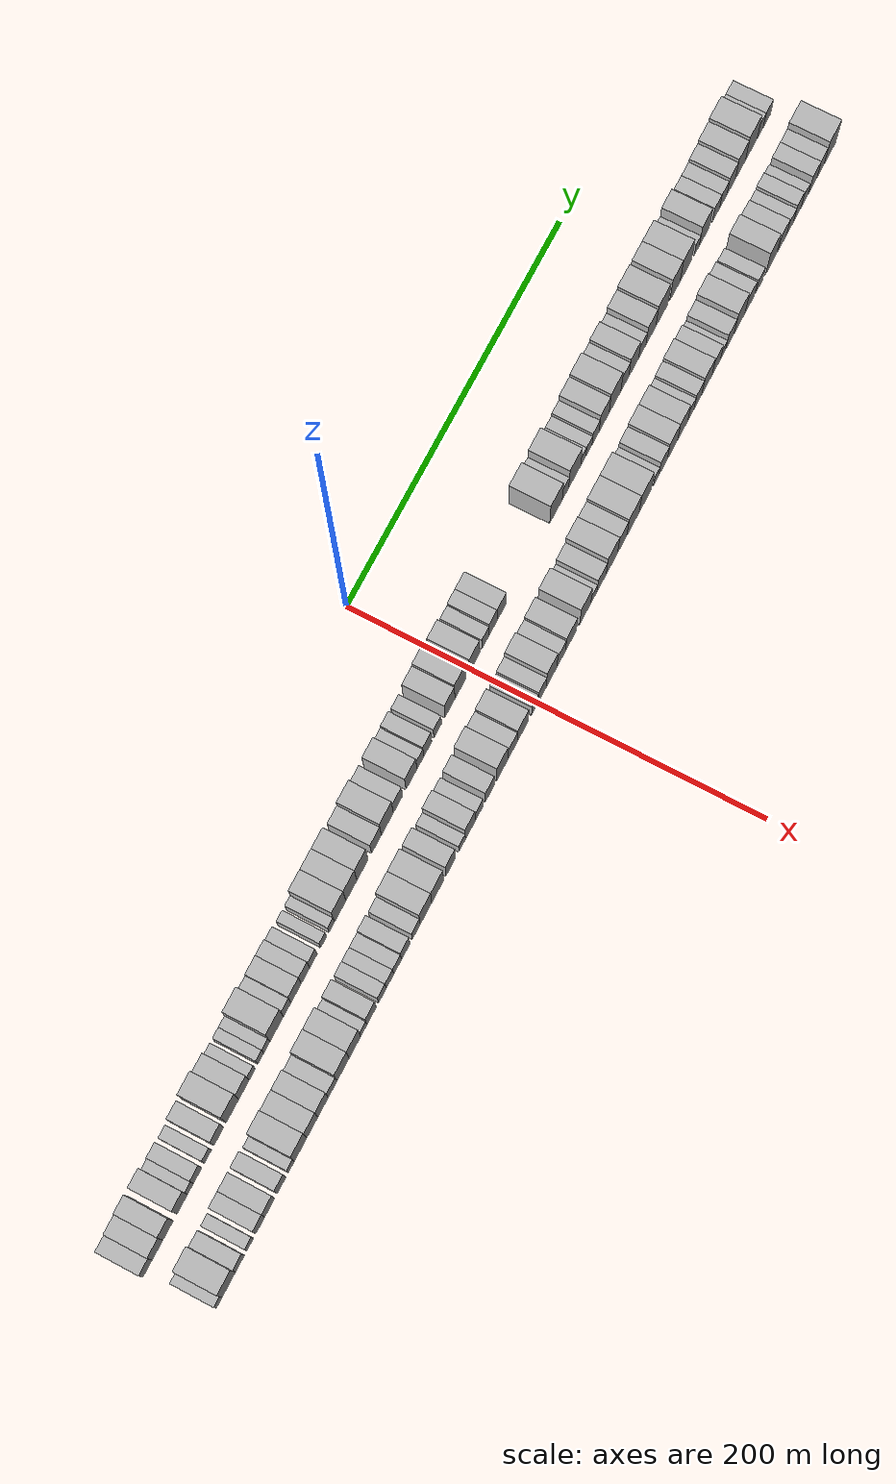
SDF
<sdf version="1.6">
 <world name="default">
  <scene>
   <sky><clouds><speed>12</speed></clouds></sky>
   <ambient>0.4 0.4 0.4 1</ambient>
   <background>0.7 0.7 0.7 1</background>
   <shadows>1</shadows>
  </scene>
  <gravity>0 0 -9.8066</gravity>
  <magnetic_field>6e-06 2.3e-05 -4.2e-05</magnetic_field>
  <physics default="0" name="default_physics" type="ode">
   <ode>
    <solver>
     <type>quick</type>
     <iters>10</iters>
     <sor>1.0</sor>
     <use_dynamic_moi_rescaling>0</use_dynamic_moi_rescaling>
    </solver>
    <constraints>
     <cfm>0</cfm>
     <erp>0.2</erp>
     <contact_max_correcting_vel>100</contact_max_correcting_vel>
     <contact_surface_layer>0.001</contact_surface_layer>
    </constraints>
   </ode>
   <max_step_size>0.004</max_step_size>
   <real_time_factor>1</real_time_factor>
   <real_time_update_rate>250</real_time_update_rate>
  </physics>
  <light name="sun" type="directional">
   <pose>0 0 10 0 0 0</pose>
   <diffuse>0.8 0.8 0.8 1</diffuse>
   <specular>0.2 0.2 0.2 1</specular>
   <attenuation>
    <range>1000</range>
    <constant>0.9</constant>
    <linear>0.01</linear>
    <quadratic>0.001</quadratic>
   </attenuation>
   <direction>-0.5 0.1 -0.9</direction>
  </light>
  <model name="building_1">
   <static>1</static>
   <pose>50.0000 -280.2556 0 0.000000 0.000000 0.000000</pose>
   <link name="link">
    <pose>0 0 7.50 0 0 0</pose>
    <collision name="collision"><geometry><box><size>20.0000 7.4888 15.0000</size></box></geometry></collision>
    <visual name="visual">
     <cast_shadows>0</cast_shadows>
     <geometry><box><size>20.0000 7.4888 15.0000</size></box></geometry>
     <material>
      <script>
       <uri>model://HANNAS_wall/materials/scripts</uri>
       <uri>model://HANNAS_wall/materials/textures</uri>
       <name>vrc/HANNAS_wall</name>
      </script>
     </material>
    </visual>
   </link>
  </model>
  <model name="building_2">
   <static>1</static>
   <pose>50.0000 -272.0830 0 0.000000 0.000000 0.000000</pose>
   <link name="link">
    <pose>0 0 9.00 0 0 0</pose>
    <collision name="collision"><geometry><box><size>20.0000 8.8564 18.0000</size></box></geometry></collision>
    <visual name="visual">
     <cast_shadows>0</cast_shadows>
     <geometry><box><size>20.0000 8.8564 18.0000</size></box></geometry>
     <material>
      <script>
       <uri>model://HANNAS_wall/materials/scripts</uri>
       <uri>model://HANNAS_wall/materials/textures</uri>
       <name>vrc/HANNAS_wall</name>
      </script>
     </material>
    </visual>
   </link>
  </model>
  <model name="building_3">
   <static>1</static>
   <pose>50.0000 -263.3895 0 0.000000 0.000000 0.000000</pose>
   <link name="link">
    <pose>0 0 10.50 0 0 0</pose>
    <collision name="collision"><geometry><box><size>20.0000 8.5307 21.0000</size></box></geometry></collision>
    <visual name="visual">
     <cast_shadows>0</cast_shadows>
     <geometry><box><size>20.0000 8.5307 21.0000</size></box></geometry>
     <material>
      <script>
       <uri>model://HANNAS_wall/materials/scripts</uri>
       <uri>model://HANNAS_wall/materials/textures</uri>
       <name>vrc/HANNAS_wall</name>
      </script>
     </material>
    </visual>
   </link>
  </model>
  <model name="building_4">
   <static>1</static>
   <pose>50.0000 -251.7585 0 0.000000 0.000000 0.000000</pose>
   <link name="link">
    <pose>0 0 10.50 0 0 0</pose>
    <collision name="collision"><geometry><box><size>20.0000 8.7313 21.0000</size></box></geometry></collision>
    <visual name="visual">
     <cast_shadows>0</cast_shadows>
     <geometry><box><size>20.0000 8.7313 21.0000</size></box></geometry>
     <material>
      <script>
       <uri>model://HANNAS_wall/materials/scripts</uri>
       <uri>model://HANNAS_wall/materials/textures</uri>
       <name>vrc/HANNAS_wall</name>
      </script>
     </material>
    </visual>
   </link>
  </model>
  <model name="building_5">
   <static>1</static>
   <pose>50.0000 -244.9554 0 0.000000 0.000000 0.000000</pose>
   <link name="link">
    <pose>0 0 6.00 0 0 0</pose>
    <collision name="collision"><geometry><box><size>20.0000 4.8749 12.0000</size></box></geometry></collision>
    <visual name="visual">
     <cast_shadows>0</cast_shadows>
     <geometry><box><size>20.0000 4.8749 12.0000</size></box></geometry>
     <material>
      <script>
       <uri>model://HANNAS_wall/materials/scripts</uri>
       <uri>model://HANNAS_wall/materials/textures</uri>
       <name>vrc/HANNAS_wall</name>
      </script>
     </material>
    </visual>
   </link>
  </model>
  <model name="building_6">
   <static>1</static>
   <pose>50.0000 -238.9676 0 0.000000 0.000000 0.000000</pose>
   <link name="link">
    <pose>0 0 7.50 0 0 0</pose>
    <collision name="collision"><geometry><box><size>20.0000 7.1007 15.0000</size></box></geometry></collision>
    <visual name="visual">
     <cast_shadows>0</cast_shadows>
     <geometry><box><size>20.0000 7.1007 15.0000</size></box></geometry>
     <material>
      <script>
       <uri>model://HANNAS_wall/materials/scripts</uri>
       <uri>model://HANNAS_wall/materials/textures</uri>
       <name>vrc/HANNAS_wall</name>
      </script>
     </material>
    </visual>
   </link>
  </model>
  <model name="building_7">
   <static>1</static>
   <pose>50.0000 -230.4224 0 0.000000 0.000000 0.000000</pose>
   <link name="link">
    <pose>0 0 6.00 0 0 0</pose>
    <collision name="collision"><geometry><box><size>20.0000 5.9898 12.0000</size></box></geometry></collision>
    <visual name="visual">
     <cast_shadows>0</cast_shadows>
     <geometry><box><size>20.0000 5.9898 12.0000</size></box></geometry>
     <material>
      <script>
       <uri>model://HANNAS_wall/materials/scripts</uri>
       <uri>model://HANNAS_wall/materials/textures</uri>
       <name>vrc/HANNAS_wall</name>
      </script>
     </material>
    </visual>
   </link>
  </model>
  <model name="building_8">
   <static>1</static>
   <pose>50.0000 -221.2836 0 0.000000 0.000000 0.000000</pose>
   <link name="link">
    <pose>0 0 9.00 0 0 0</pose>
    <collision name="collision"><geometry><box><size>20.0000 8.2877 18.0000</size></box></geometry></collision>
    <visual name="visual">
     <cast_shadows>0</cast_shadows>
     <geometry><box><size>20.0000 8.2877 18.0000</size></box></geometry>
     <material>
      <script>
       <uri>model://HANNAS_wall/materials/scripts</uri>
       <uri>model://HANNAS_wall/materials/textures</uri>
       <name>vrc/HANNAS_wall</name>
      </script>
     </material>
    </visual>
   </link>
  </model>
  <model name="building_9">
   <static>1</static>
   <pose>50.0000 -209.7716 0 0.000000 0.000000 0.000000</pose>
   <link name="link">
    <pose>0 0 12.00 0 0 0</pose>
    <collision name="collision"><geometry><box><size>20.0000 10.7363 24.0000</size></box></geometry></collision>
    <visual name="visual">
     <cast_shadows>0</cast_shadows>
     <geometry><box><size>20.0000 10.7363 24.0000</size></box></geometry>
     <material>
      <script>
       <uri>model://HANNAS_wall/materials/scripts</uri>
       <uri>model://HANNAS_wall/materials/textures</uri>
       <name>vrc/HANNAS_wall</name>
      </script>
     </material>
    </visual>
   </link>
  </model>
  <model name="building_10">
   <static>1</static>
   <pose>50.0000 -200.0302 0 0.000000 0.000000 0.000000</pose>
   <link name="link">
    <pose>0 0 9.00 0 0 0</pose>
    <collision name="collision"><geometry><box><size>20.0000 8.7464 18.0000</size></box></geometry></collision>
    <visual name="visual">
     <cast_shadows>0</cast_shadows>
     <geometry><box><size>20.0000 8.7464 18.0000</size></box></geometry>
     <material>
      <script>
       <uri>model://HANNAS_wall/materials/scripts</uri>
       <uri>model://HANNAS_wall/materials/textures</uri>
       <name>vrc/HANNAS_wall</name>
      </script>
     </material>
    </visual>
   </link>
  </model>
  <model name="building_11">
   <static>1</static>
   <pose>50.0000 -193.0327 0 0.000000 0.000000 0.000000</pose>
   <link name="link">
    <pose>0 0 6.00 0 0 0</pose>
    <collision name="collision"><geometry><box><size>20.0000 5.2487 12.0000</size></box></geometry></collision>
    <visual name="visual">
     <cast_shadows>0</cast_shadows>
     <geometry><box><size>20.0000 5.2487 12.0000</size></box></geometry>
     <material>
      <script>
       <uri>model://HANNAS_wall/materials/scripts</uri>
       <uri>model://HANNAS_wall/materials/textures</uri>
       <name>vrc/HANNAS_wall</name>
      </script>
     </material>
    </visual>
   </link>
  </model>
  <model name="building_12">
   <static>1</static>
   <pose>50.0000 -185.8474 0 0.000000 0.000000 0.000000</pose>
   <link name="link">
    <pose>0 0 6.00 0 0 0</pose>
    <collision name="collision"><geometry><box><size>20.0000 5.1220 12.0000</size></box></geometry></collision>
    <visual name="visual">
     <cast_shadows>0</cast_shadows>
     <geometry><box><size>20.0000 5.1220 12.0000</size></box></geometry>
     <material>
      <script>
       <uri>model://HANNAS_wall/materials/scripts</uri>
       <uri>model://HANNAS_wall/materials/textures</uri>
       <name>vrc/HANNAS_wall</name>
      </script>
     </material>
    </visual>
   </link>
  </model>
  <model name="building_13">
   <static>1</static>
   <pose>50.0000 -180.6477 0 0.000000 0.000000 0.000000</pose>
   <link name="link">
    <pose>0 0 6.00 0 0 0</pose>
    <collision name="collision"><geometry><box><size>20.0000 5.2775 12.0000</size></box></geometry></collision>
    <visual name="visual">
     <cast_shadows>0</cast_shadows>
     <geometry><box><size>20.0000 5.2775 12.0000</size></box></geometry>
     <material>
      <script>
       <uri>model://HANNAS_wall/materials/scripts</uri>
       <uri>model://HANNAS_wall/materials/textures</uri>
       <name>vrc/HANNAS_wall</name>
      </script>
     </material>
    </visual>
   </link>
  </model>
  <model name="building_14">
   <static>1</static>
   <pose>50.0000 -172.2287 0 0.000000 0.000000 0.000000</pose>
   <link name="link">
    <pose>0 0 12.00 0 0 0</pose>
    <collision name="collision"><geometry><box><size>20.0000 11.5604 24.0000</size></box></geometry></collision>
    <visual name="visual">
     <cast_shadows>0</cast_shadows>
     <geometry><box><size>20.0000 11.5604 24.0000</size></box></geometry>
     <material>
      <script>
       <uri>model://HANNAS_wall/materials/scripts</uri>
       <uri>model://HANNAS_wall/materials/textures</uri>
       <name>vrc/HANNAS_wall</name>
      </script>
     </material>
    </visual>
   </link>
  </model>
  <model name="building_15">
   <static>1</static>
   <pose>50.0000 -163.2414 0 0.000000 0.000000 0.000000</pose>
   <link name="link">
    <pose>0 0 7.50 0 0 0</pose>
    <collision name="collision"><geometry><box><size>20.0000 6.4141 15.0000</size></box></geometry></collision>
    <visual name="visual">
     <cast_shadows>0</cast_shadows>
     <geometry><box><size>20.0000 6.4141 15.0000</size></box></geometry>
     <material>
      <script>
       <uri>model://HANNAS_wall/materials/scripts</uri>
       <uri>model://HANNAS_wall/materials/textures</uri>
       <name>vrc/HANNAS_wall</name>
      </script>
     </material>
    </visual>
   </link>
  </model>
  <model name="building_16">
   <static>1</static>
   <pose>50.0000 -155.5923 0 0.000000 0.000000 0.000000</pose>
   <link name="link">
    <pose>0 0 9.00 0 0 0</pose>
    <collision name="collision"><geometry><box><size>20.0000 8.8841 18.0000</size></box></geometry></collision>
    <visual name="visual">
     <cast_shadows>0</cast_shadows>
     <geometry><box><size>20.0000 8.8841 18.0000</size></box></geometry>
     <material>
      <script>
       <uri>model://HANNAS_wall/materials/scripts</uri>
       <uri>model://HANNAS_wall/materials/textures</uri>
       <name>vrc/HANNAS_wall</name>
      </script>
     </material>
    </visual>
   </link>
  </model>
  <model name="building_17">
   <static>1</static>
   <pose>50.0000 -147.4946 0 0.000000 0.000000 0.000000</pose>
   <link name="link">
    <pose>0 0 9.00 0 0 0</pose>
    <collision name="collision"><geometry><box><size>20.0000 7.3115 18.0000</size></box></geometry></collision>
    <visual name="visual">
     <cast_shadows>0</cast_shadows>
     <geometry><box><size>20.0000 7.3115 18.0000</size></box></geometry>
     <material>
      <script>
       <uri>model://HANNAS_wall/materials/scripts</uri>
       <uri>model://HANNAS_wall/materials/textures</uri>
       <name>vrc/HANNAS_wall</name>
      </script>
     </material>
    </visual>
   </link>
  </model>
  <model name="building_18">
   <static>1</static>
   <pose>50.0000 -140.6192 0 0.000000 0.000000 0.000000</pose>
   <link name="link">
    <pose>0 0 7.50 0 0 0</pose>
    <collision name="collision"><geometry><box><size>20.0000 6.4392 15.0000</size></box></geometry></collision>
    <visual name="visual">
     <cast_shadows>0</cast_shadows>
     <geometry><box><size>20.0000 6.4392 15.0000</size></box></geometry>
     <material>
      <script>
       <uri>model://HANNAS_wall/materials/scripts</uri>
       <uri>model://HANNAS_wall/materials/textures</uri>
       <name>vrc/HANNAS_wall</name>
      </script>
     </material>
    </visual>
   </link>
  </model>
  <model name="building_19">
   <static>1</static>
   <pose>50.0000 -131.7862 0 0.000000 0.000000 0.000000</pose>
   <link name="link">
    <pose>0 0 6.00 0 0 0</pose>
    <collision name="collision"><geometry><box><size>20.0000 5.2268 12.0000</size></box></geometry></collision>
    <visual name="visual">
     <cast_shadows>0</cast_shadows>
     <geometry><box><size>20.0000 5.2268 12.0000</size></box></geometry>
     <material>
      <script>
       <uri>model://HANNAS_wall/materials/scripts</uri>
       <uri>model://HANNAS_wall/materials/textures</uri>
       <name>vrc/HANNAS_wall</name>
      </script>
     </material>
    </visual>
   </link>
  </model>
  <model name="building_20">
   <static>1</static>
   <pose>50.0000 -124.7608 0 0.000000 0.000000 0.000000</pose>
   <link name="link">
    <pose>0 0 6.00 0 0 0</pose>
    <collision name="collision"><geometry><box><size>20.0000 4.8239 12.0000</size></box></geometry></collision>
    <visual name="visual">
     <cast_shadows>0</cast_shadows>
     <geometry><box><size>20.0000 4.8239 12.0000</size></box></geometry>
     <material>
      <script>
       <uri>model://HANNAS_wall/materials/scripts</uri>
       <uri>model://HANNAS_wall/materials/textures</uri>
       <name>vrc/HANNAS_wall</name>
      </script>
     </material>
    </visual>
   </link>
  </model>
  <model name="building_21">
   <static>1</static>
   <pose>50.0000 -117.3634 0 0.000000 0.000000 0.000000</pose>
   <link name="link">
    <pose>0 0 12.00 0 0 0</pose>
    <collision name="collision"><geometry><box><size>20.0000 9.9710 24.0000</size></box></geometry></collision>
    <visual name="visual">
     <cast_shadows>0</cast_shadows>
     <geometry><box><size>20.0000 9.9710 24.0000</size></box></geometry>
     <material>
      <script>
       <uri>model://HANNAS_wall/materials/scripts</uri>
       <uri>model://HANNAS_wall/materials/textures</uri>
       <name>vrc/HANNAS_wall</name>
      </script>
     </material>
    </visual>
   </link>
  </model>
  <model name="building_22">
   <static>1</static>
   <pose>50.0000 -107.5309 0 0.000000 0.000000 0.000000</pose>
   <link name="link">
    <pose>0 0 12.00 0 0 0</pose>
    <collision name="collision"><geometry><box><size>20.0000 9.6939 24.0000</size></box></geometry></collision>
    <visual name="visual">
     <cast_shadows>0</cast_shadows>
     <geometry><box><size>20.0000 9.6939 24.0000</size></box></geometry>
     <material>
      <script>
       <uri>model://HANNAS_wall/materials/scripts</uri>
       <uri>model://HANNAS_wall/materials/textures</uri>
       <name>vrc/HANNAS_wall</name>
      </script>
     </material>
    </visual>
   </link>
  </model>
  <model name="building_23">
   <static>1</static>
   <pose>50.0000 -97.7347 0 0.000000 0.000000 0.000000</pose>
   <link name="link">
    <pose>0 0 12.00 0 0 0</pose>
    <collision name="collision"><geometry><box><size>20.0000 9.8984 24.0000</size></box></geometry></collision>
    <visual name="visual">
     <cast_shadows>0</cast_shadows>
     <geometry><box><size>20.0000 9.8984 24.0000</size></box></geometry>
     <material>
      <script>
       <uri>model://HANNAS_wall/materials/scripts</uri>
       <uri>model://HANNAS_wall/materials/textures</uri>
       <name>vrc/HANNAS_wall</name>
      </script>
     </material>
    </visual>
   </link>
  </model>
  <model name="building_24">
   <static>1</static>
   <pose>50.0000 -85.4535 0 0.000000 0.000000 0.000000</pose>
   <link name="link">
    <pose>0 0 9.00 0 0 0</pose>
    <collision name="collision"><geometry><box><size>20.0000 8.6641 18.0000</size></box></geometry></collision>
    <visual name="visual">
     <cast_shadows>0</cast_shadows>
     <geometry><box><size>20.0000 8.6641 18.0000</size></box></geometry>
     <material>
      <script>
       <uri>model://HANNAS_wall/materials/scripts</uri>
       <uri>model://HANNAS_wall/materials/textures</uri>
       <name>vrc/HANNAS_wall</name>
      </script>
     </material>
    </visual>
   </link>
  </model>
  <model name="building_25">
   <static>1</static>
   <pose>50.0000 -75.7905 0 0.000000 0.000000 0.000000</pose>
   <link name="link">
    <pose>0 0 12.00 0 0 0</pose>
    <collision name="collision"><geometry><box><size>20.0000 10.6619 24.0000</size></box></geometry></collision>
    <visual name="visual">
     <cast_shadows>0</cast_shadows>
     <geometry><box><size>20.0000 10.6619 24.0000</size></box></geometry>
     <material>
      <script>
       <uri>model://HANNAS_wall/materials/scripts</uri>
       <uri>model://HANNAS_wall/materials/textures</uri>
       <name>vrc/HANNAS_wall</name>
      </script>
     </material>
    </visual>
   </link>
  </model>
  <model name="building_26">
   <static>1</static>
   <pose>50.0000 -66.2932 0 0.000000 0.000000 0.000000</pose>
   <link name="link">
    <pose>0 0 9.00 0 0 0</pose>
    <collision name="collision"><geometry><box><size>20.0000 8.3327 18.0000</size></box></geometry></collision>
    <visual name="visual">
     <cast_shadows>0</cast_shadows>
     <geometry><box><size>20.0000 8.3327 18.0000</size></box></geometry>
     <material>
      <script>
       <uri>model://HANNAS_wall/materials/scripts</uri>
       <uri>model://HANNAS_wall/materials/textures</uri>
       <name>vrc/HANNAS_wall</name>
      </script>
     </material>
    </visual>
   </link>
  </model>
  <model name="building_27">
   <static>1</static>
   <pose>50.0000 -54.2423 0 0.000000 0.000000 0.000000</pose>
   <link name="link">
    <pose>0 0 10.50 0 0 0</pose>
    <collision name="collision"><geometry><box><size>20.0000 9.7691 21.0000</size></box></geometry></collision>
    <visual name="visual">
     <cast_shadows>0</cast_shadows>
     <geometry><box><size>20.0000 9.7691 21.0000</size></box></geometry>
     <material>
      <script>
       <uri>model://HANNAS_wall/materials/scripts</uri>
       <uri>model://HANNAS_wall/materials/textures</uri>
       <name>vrc/HANNAS_wall</name>
      </script>
     </material>
    </visual>
   </link>
  </model>
  <model name="building_28">
   <static>1</static>
   <pose>50.0000 -46.3320 0 0.000000 0.000000 0.000000</pose>
   <link name="link">
    <pose>0 0 7.50 0 0 0</pose>
    <collision name="collision"><geometry><box><size>20.0000 6.0516 15.0000</size></box></geometry></collision>
    <visual name="visual">
     <cast_shadows>0</cast_shadows>
     <geometry><box><size>20.0000 6.0516 15.0000</size></box></geometry>
     <material>
      <script>
       <uri>model://HANNAS_wall/materials/scripts</uri>
       <uri>model://HANNAS_wall/materials/textures</uri>
       <name>vrc/HANNAS_wall</name>
      </script>
     </material>
    </visual>
   </link>
  </model>
  <model name="building_29">
   <static>1</static>
   <pose>50.0000 -39.6737 0 0.000000 0.000000 0.000000</pose>
   <link name="link">
    <pose>0 0 9.00 0 0 0</pose>
    <collision name="collision"><geometry><box><size>20.0000 7.2651 18.0000</size></box></geometry></collision>
    <visual name="visual">
     <cast_shadows>0</cast_shadows>
     <geometry><box><size>20.0000 7.2651 18.0000</size></box></geometry>
     <material>
      <script>
       <uri>model://HANNAS_wall/materials/scripts</uri>
       <uri>model://HANNAS_wall/materials/textures</uri>
       <name>vrc/HANNAS_wall</name>
      </script>
     </material>
    </visual>
   </link>
  </model>
  <model name="building_30">
   <static>1</static>
   <pose>50.0000 -30.5757 0 0.000000 0.000000 0.000000</pose>
   <link name="link">
    <pose>0 0 7.50 0 0 0</pose>
    <collision name="collision"><geometry><box><size>20.0000 6.9310 15.0000</size></box></geometry></collision>
    <visual name="visual">
     <cast_shadows>0</cast_shadows>
     <geometry><box><size>20.0000 6.9310 15.0000</size></box></geometry>
     <material>
      <script>
       <uri>model://HANNAS_wall/materials/scripts</uri>
       <uri>model://HANNAS_wall/materials/textures</uri>
       <name>vrc/HANNAS_wall</name>
      </script>
     </material>
    </visual>
   </link>
  </model>
  <model name="building_31">
   <static>1</static>
   <pose>50.0000 -19.5332 0 0.000000 0.000000 0.000000</pose>
   <link name="link">
    <pose>0 0 10.50 0 0 0</pose>
    <collision name="collision"><geometry><box><size>20.0000 9.1540 21.0000</size></box></geometry></collision>
    <visual name="visual">
     <cast_shadows>0</cast_shadows>
     <geometry><box><size>20.0000 9.1540 21.0000</size></box></geometry>
     <material>
      <script>
       <uri>model://HANNAS_wall/materials/scripts</uri>
       <uri>model://HANNAS_wall/materials/textures</uri>
       <name>vrc/HANNAS_wall</name>
      </script>
     </material>
    </visual>
   </link>
  </model>
  <model name="building_32">
   <static>1</static>
   <pose>50.0000 -9.8697 0 0.000000 0.000000 0.000000</pose>
   <link name="link">
    <pose>0 0 12.00 0 0 0</pose>
    <collision name="collision"><geometry><box><size>20.0000 10.1728 24.0000</size></box></geometry></collision>
    <visual name="visual">
     <cast_shadows>0</cast_shadows>
     <geometry><box><size>20.0000 10.1728 24.0000</size></box></geometry>
     <material>
      <script>
       <uri>model://HANNAS_wall/materials/scripts</uri>
       <uri>model://HANNAS_wall/materials/textures</uri>
       <name>vrc/HANNAS_wall</name>
      </script>
     </material>
    </visual>
   </link>
  </model>
  <model name="building_33">
   <static>1</static>
   <pose>50.0000 2.9684 0 0.000000 0.000000 0.000000</pose>
   <link name="link">
    <pose>0 0 10.50 0 0 0</pose>
    <collision name="collision"><geometry><box><size>20.0000 9.5035 21.0000</size></box></geometry></collision>
    <visual name="visual">
     <cast_shadows>0</cast_shadows>
     <geometry><box><size>20.0000 9.5035 21.0000</size></box></geometry>
     <material>
      <script>
       <uri>model://HANNAS_wall/materials/scripts</uri>
       <uri>model://HANNAS_wall/materials/textures</uri>
       <name>vrc/HANNAS_wall</name>
      </script>
     </material>
    </visual>
   </link>
  </model>
  <model name="building_34">
   <static>1</static>
   <pose>50.0000 13.0650 0 0.000000 0.000000 0.000000</pose>
   <link name="link">
    <pose>0 0 7.50 0 0 0</pose>
    <collision name="collision"><geometry><box><size>20.0000 6.6897 15.0000</size></box></geometry></collision>
    <visual name="visual">
     <cast_shadows>0</cast_shadows>
     <geometry><box><size>20.0000 6.6897 15.0000</size></box></geometry>
     <material>
      <script>
       <uri>model://HANNAS_wall/materials/scripts</uri>
       <uri>model://HANNAS_wall/materials/textures</uri>
       <name>vrc/HANNAS_wall</name>
      </script>
     </material>
    </visual>
   </link>
  </model>
  <model name="building_35">
   <static>1</static>
   <pose>50.0000 20.0244 0 0.000000 0.000000 0.000000</pose>
   <link name="link">
    <pose>0 0 9.00 0 0 0</pose>
    <collision name="collision"><geometry><box><size>20.0000 7.2292 18.0000</size></box></geometry></collision>
    <visual name="visual">
     <cast_shadows>0</cast_shadows>
     <geometry><box><size>20.0000 7.2292 18.0000</size></box></geometry>
     <material>
      <script>
       <uri>model://HANNAS_wall/materials/scripts</uri>
       <uri>model://HANNAS_wall/materials/textures</uri>
       <name>vrc/HANNAS_wall</name>
      </script>
     </material>
    </visual>
   </link>
  </model>
  <model name="building_36">
   <static>1</static>
   <pose>50.0000 27.8837 0 0.000000 0.000000 0.000000</pose>
   <link name="link">
    <pose>0 0 9.00 0 0 0</pose>
    <collision name="collision"><geometry><box><size>20.0000 8.4892 18.0000</size></box></geometry></collision>
    <visual name="visual">
     <cast_shadows>0</cast_shadows>
     <geometry><box><size>20.0000 8.4892 18.0000</size></box></geometry>
     <material>
      <script>
       <uri>model://HANNAS_wall/materials/scripts</uri>
       <uri>model://HANNAS_wall/materials/textures</uri>
       <name>vrc/HANNAS_wall</name>
      </script>
     </material>
    </visual>
   </link>
  </model>
  <model name="building_37">
   <static>1</static>
   <pose>50.0000 78.7567 0 0.000000 0.000000 0.000000</pose>
   <link name="link">
    <pose>0 0 12.00 0 0 0</pose>
    <collision name="collision"><geometry><box><size>20.0000 11.7523 24.0000</size></box></geometry></collision>
    <visual name="visual">
     <cast_shadows>0</cast_shadows>
     <geometry><box><size>20.0000 11.7523 24.0000</size></box></geometry>
     <material>
      <script>
       <uri>model://HANNAS_wall/materials/scripts</uri>
       <uri>model://HANNAS_wall/materials/textures</uri>
       <name>vrc/HANNAS_wall</name>
      </script>
     </material>
    </visual>
   </link>
  </model>
  <model name="building_38">
   <static>1</static>
   <pose>50.0000 87.6733 0 0.000000 0.000000 0.000000</pose>
   <link name="link">
    <pose>0 0 7.50 0 0 0</pose>
    <collision name="collision"><geometry><box><size>20.0000 6.0810 15.0000</size></box></geometry></collision>
    <visual name="visual">
     <cast_shadows>0</cast_shadows>
     <geometry><box><size>20.0000 6.0810 15.0000</size></box></geometry>
     <material>
      <script>
       <uri>model://HANNAS_wall/materials/scripts</uri>
       <uri>model://HANNAS_wall/materials/textures</uri>
       <name>vrc/HANNAS_wall</name>
      </script>
     </material>
    </visual>
   </link>
  </model>
  <model name="building_39">
   <static>1</static>
   <pose>50.0000 96.4820 0 0.000000 0.000000 0.000000</pose>
   <link name="link">
    <pose>0 0 12.00 0 0 0</pose>
    <collision name="collision"><geometry><box><size>20.0000 11.5364 24.0000</size></box></geometry></collision>
    <visual name="visual">
     <cast_shadows>0</cast_shadows>
     <geometry><box><size>20.0000 11.5364 24.0000</size></box></geometry>
     <material>
      <script>
       <uri>model://HANNAS_wall/materials/scripts</uri>
       <uri>model://HANNAS_wall/materials/textures</uri>
       <name>vrc/HANNAS_wall</name>
      </script>
     </material>
    </visual>
   </link>
  </model>
  <model name="building_40">
   <static>1</static>
   <pose>50.0000 104.6592 0 0.000000 0.000000 0.000000</pose>
   <link name="link">
    <pose>0 0 6.00 0 0 0</pose>
    <collision name="collision"><geometry><box><size>20.0000 4.8180 12.0000</size></box></geometry></collision>
    <visual name="visual">
     <cast_shadows>0</cast_shadows>
     <geometry><box><size>20.0000 4.8180 12.0000</size></box></geometry>
     <material>
      <script>
       <uri>model://HANNAS_wall/materials/scripts</uri>
       <uri>model://HANNAS_wall/materials/textures</uri>
       <name>vrc/HANNAS_wall</name>
      </script>
     </material>
    </visual>
   </link>
  </model>
  <model name="building_41">
   <static>1</static>
   <pose>50.0000 110.0333 0 0.000000 0.000000 0.000000</pose>
   <link name="link">
    <pose>0 0 6.00 0 0 0</pose>
    <collision name="collision"><geometry><box><size>20.0000 5.9301 12.0000</size></box></geometry></collision>
    <visual name="visual">
     <cast_shadows>0</cast_shadows>
     <geometry><box><size>20.0000 5.9301 12.0000</size></box></geometry>
     <material>
      <script>
       <uri>model://HANNAS_wall/materials/scripts</uri>
       <uri>model://HANNAS_wall/materials/textures</uri>
       <name>vrc/HANNAS_wall</name>
      </script>
     </material>
    </visual>
   </link>
  </model>
  <model name="building_42">
   <static>1</static>
   <pose>50.0000 116.3993 0 0.000000 0.000000 0.000000</pose>
   <link name="link">
    <pose>0 0 7.50 0 0 0</pose>
    <collision name="collision"><geometry><box><size>20.0000 6.8020 15.0000</size></box></geometry></collision>
    <visual name="visual">
     <cast_shadows>0</cast_shadows>
     <geometry><box><size>20.0000 6.8020 15.0000</size></box></geometry>
     <material>
      <script>
       <uri>model://HANNAS_wall/materials/scripts</uri>
       <uri>model://HANNAS_wall/materials/textures</uri>
       <name>vrc/HANNAS_wall</name>
      </script>
     </material>
    </visual>
   </link>
  </model>
  <model name="building_43">
   <static>1</static>
   <pose>50.0000 124.5717 0 0.000000 0.000000 0.000000</pose>
   <link name="link">
    <pose>0 0 10.50 0 0 0</pose>
    <collision name="collision"><geometry><box><size>20.0000 9.5428 21.0000</size></box></geometry></collision>
    <visual name="visual">
     <cast_shadows>0</cast_shadows>
     <geometry><box><size>20.0000 9.5428 21.0000</size></box></geometry>
     <material>
      <script>
       <uri>model://HANNAS_wall/materials/scripts</uri>
       <uri>model://HANNAS_wall/materials/textures</uri>
       <name>vrc/HANNAS_wall</name>
      </script>
     </material>
    </visual>
   </link>
  </model>
  <model name="building_44">
   <static>1</static>
   <pose>50.0000 134.9854 0 0.000000 0.000000 0.000000</pose>
   <link name="link">
    <pose>0 0 12.00 0 0 0</pose>
    <collision name="collision"><geometry><box><size>20.0000 11.2845 24.0000</size></box></geometry></collision>
    <visual name="visual">
     <cast_shadows>0</cast_shadows>
     <geometry><box><size>20.0000 11.2845 24.0000</size></box></geometry>
     <material>
      <script>
       <uri>model://HANNAS_wall/materials/scripts</uri>
       <uri>model://HANNAS_wall/materials/textures</uri>
       <name>vrc/HANNAS_wall</name>
      </script>
     </material>
    </visual>
   </link>
  </model>
  <model name="building_45">
   <static>1</static>
   <pose>50.0000 144.5385 0 0.000000 0.000000 0.000000</pose>
   <link name="link">
    <pose>0 0 9.00 0 0 0</pose>
    <collision name="collision"><geometry><box><size>20.0000 7.8218 18.0000</size></box></geometry></collision>
    <visual name="visual">
     <cast_shadows>0</cast_shadows>
     <geometry><box><size>20.0000 7.8218 18.0000</size></box></geometry>
     <material>
      <script>
       <uri>model://HANNAS_wall/materials/scripts</uri>
       <uri>model://HANNAS_wall/materials/textures</uri>
       <name>vrc/HANNAS_wall</name>
      </script>
     </material>
    </visual>
   </link>
  </model>
  <model name="building_46">
   <static>1</static>
   <pose>50.0000 153.2001 0 0.000000 0.000000 0.000000</pose>
   <link name="link">
    <pose>0 0 10.50 0 0 0</pose>
    <collision name="collision"><geometry><box><size>20.0000 9.5014 21.0000</size></box></geometry></collision>
    <visual name="visual">
     <cast_shadows>0</cast_shadows>
     <geometry><box><size>20.0000 9.5014 21.0000</size></box></geometry>
     <material>
      <script>
       <uri>model://HANNAS_wall/materials/scripts</uri>
       <uri>model://HANNAS_wall/materials/textures</uri>
       <name>vrc/HANNAS_wall</name>
      </script>
     </material>
    </visual>
   </link>
  </model>
  <model name="building_47">
   <static>1</static>
   <pose>50.0000 161.5398 0 0.000000 0.000000 0.000000</pose>
   <link name="link">
    <pose>0 0 7.50 0 0 0</pose>
    <collision name="collision"><geometry><box><size>20.0000 7.1778 15.0000</size></box></geometry></collision>
    <visual name="visual">
     <cast_shadows>0</cast_shadows>
     <geometry><box><size>20.0000 7.1778 15.0000</size></box></geometry>
     <material>
      <script>
       <uri>model://HANNAS_wall/materials/scripts</uri>
       <uri>model://HANNAS_wall/materials/textures</uri>
       <name>vrc/HANNAS_wall</name>
      </script>
     </material>
    </visual>
   </link>
  </model>
  <model name="building_48">
   <static>1</static>
   <pose>50.0000 169.8752 0 0.000000 0.000000 0.000000</pose>
   <link name="link">
    <pose>0 0 10.50 0 0 0</pose>
    <collision name="collision"><geometry><box><size>20.0000 9.4931 21.0000</size></box></geometry></collision>
    <visual name="visual">
     <cast_shadows>0</cast_shadows>
     <geometry><box><size>20.0000 9.4931 21.0000</size></box></geometry>
     <material>
      <script>
       <uri>model://HANNAS_wall/materials/scripts</uri>
       <uri>model://HANNAS_wall/materials/textures</uri>
       <name>vrc/HANNAS_wall</name>
      </script>
     </material>
    </visual>
   </link>
  </model>
  <model name="building_49">
   <static>1</static>
   <pose>50.0000 180.5172 0 0.000000 0.000000 0.000000</pose>
   <link name="link">
    <pose>0 0 12.00 0 0 0</pose>
    <collision name="collision"><geometry><box><size>20.0000 11.7908 24.0000</size></box></geometry></collision>
    <visual name="visual">
     <cast_shadows>0</cast_shadows>
     <geometry><box><size>20.0000 11.7908 24.0000</size></box></geometry>
     <material>
      <script>
       <uri>model://HANNAS_wall/materials/scripts</uri>
       <uri>model://HANNAS_wall/materials/textures</uri>
       <name>vrc/HANNAS_wall</name>
      </script>
     </material>
    </visual>
   </link>
  </model>
  <model name="building_50">
   <static>1</static>
   <pose>50.0000 193.5483 0 0.000000 0.000000 0.000000</pose>
   <link name="link">
    <pose>0 0 12.00 0 0 0</pose>
    <collision name="collision"><geometry><box><size>20.0000 10.2715 24.0000</size></box></geometry></collision>
    <visual name="visual">
     <cast_shadows>0</cast_shadows>
     <geometry><box><size>20.0000 10.2715 24.0000</size></box></geometry>
     <material>
      <script>
       <uri>model://HANNAS_wall/materials/scripts</uri>
       <uri>model://HANNAS_wall/materials/textures</uri>
       <name>vrc/HANNAS_wall</name>
      </script>
     </material>
    </visual>
   </link>
  </model>
  <model name="building_51">
   <static>1</static>
   <pose>50.0000 204.2314 0 0.000000 0.000000 0.000000</pose>
   <link name="link">
    <pose>0 0 12.00 0 0 0</pose>
    <collision name="collision"><geometry><box><size>20.0000 11.0947 24.0000</size></box></geometry></collision>
    <visual name="visual">
     <cast_shadows>0</cast_shadows>
     <geometry><box><size>20.0000 11.0947 24.0000</size></box></geometry>
     <material>
      <script>
       <uri>model://HANNAS_wall/materials/scripts</uri>
       <uri>model://HANNAS_wall/materials/textures</uri>
       <name>vrc/HANNAS_wall</name>
      </script>
     </material>
    </visual>
   </link>
  </model>
  <model name="building_52">
   <static>1</static>
   <pose>50.0000 215.2408 0 0.000000 0.000000 0.000000</pose>
   <link name="link">
    <pose>0 0 6.00 0 0 0</pose>
    <collision name="collision"><geometry><box><size>20.0000 4.9242 12.0000</size></box></geometry></collision>
    <visual name="visual">
     <cast_shadows>0</cast_shadows>
     <geometry><box><size>20.0000 4.9242 12.0000</size></box></geometry>
     <material>
      <script>
       <uri>model://HANNAS_wall/materials/scripts</uri>
       <uri>model://HANNAS_wall/materials/textures</uri>
       <name>vrc/HANNAS_wall</name>
      </script>
     </material>
    </visual>
   </link>
  </model>
  <model name="building_53">
   <static>1</static>
   <pose>50.0000 222.7247 0 0.000000 0.000000 0.000000</pose>
   <link name="link">
    <pose>0 0 10.50 0 0 0</pose>
    <collision name="collision"><geometry><box><size>20.0000 10.0436 21.0000</size></box></geometry></collision>
    <visual name="visual">
     <cast_shadows>0</cast_shadows>
     <geometry><box><size>20.0000 10.0436 21.0000</size></box></geometry>
     <material>
      <script>
       <uri>model://HANNAS_wall/materials/scripts</uri>
       <uri>model://HANNAS_wall/materials/textures</uri>
       <name>vrc/HANNAS_wall</name>
      </script>
     </material>
    </visual>
   </link>
  </model>
  <model name="building_54">
   <static>1</static>
   <pose>50.0000 234.4221 0 0.000000 0.000000 0.000000</pose>
   <link name="link">
    <pose>0 0 7.50 0 0 0</pose>
    <collision name="collision"><geometry><box><size>20.0000 7.3512 15.0000</size></box></geometry></collision>
    <visual name="visual">
     <cast_shadows>0</cast_shadows>
     <geometry><box><size>20.0000 7.3512 15.0000</size></box></geometry>
     <material>
      <script>
       <uri>model://HANNAS_wall/materials/scripts</uri>
       <uri>model://HANNAS_wall/materials/textures</uri>
       <name>vrc/HANNAS_wall</name>
      </script>
     </material>
    </visual>
   </link>
  </model>
  <model name="building_55">
   <static>1</static>
   <pose>50.0000 241.7030 0 0.000000 0.000000 0.000000</pose>
   <link name="link">
    <pose>0 0 7.50 0 0 0</pose>
    <collision name="collision"><geometry><box><size>20.0000 7.2104 15.0000</size></box></geometry></collision>
    <visual name="visual">
     <cast_shadows>0</cast_shadows>
     <geometry><box><size>20.0000 7.2104 15.0000</size></box></geometry>
     <material>
      <script>
       <uri>model://HANNAS_wall/materials/scripts</uri>
       <uri>model://HANNAS_wall/materials/textures</uri>
       <name>vrc/HANNAS_wall</name>
      </script>
     </material>
    </visual>
   </link>
  </model>
  <model name="building_56">
   <static>1</static>
   <pose>50.0000 249.5671 0 0.000000 0.000000 0.000000</pose>
   <link name="link">
    <pose>0 0 9.00 0 0 0</pose>
    <collision name="collision"><geometry><box><size>20.0000 8.5178 18.0000</size></box></geometry></collision>
    <visual name="visual">
     <cast_shadows>0</cast_shadows>
     <geometry><box><size>20.0000 8.5178 18.0000</size></box></geometry>
     <material>
      <script>
       <uri>model://HANNAS_wall/materials/scripts</uri>
       <uri>model://HANNAS_wall/materials/textures</uri>
       <name>vrc/HANNAS_wall</name>
      </script>
     </material>
    </visual>
   </link>
  </model>
  <model name="building_57">
   <static>1</static>
   <pose>50.0000 258.9550 0 0.000000 0.000000 0.000000</pose>
   <link name="link">
    <pose>0 0 10.50 0 0 0</pose>
    <collision name="collision"><geometry><box><size>20.0000 10.2580 21.0000</size></box></geometry></collision>
    <visual name="visual">
     <cast_shadows>0</cast_shadows>
     <geometry><box><size>20.0000 10.2580 21.0000</size></box></geometry>
     <material>
      <script>
       <uri>model://HANNAS_wall/materials/scripts</uri>
       <uri>model://HANNAS_wall/materials/textures</uri>
       <name>vrc/HANNAS_wall</name>
      </script>
     </material>
    </visual>
   </link>
  </model>
  <model name="building_58">
   <static>1</static>
   <pose>50.0000 270.0629 0 0.000000 0.000000 0.000000</pose>
   <link name="link">
    <pose>0 0 12.00 0 0 0</pose>
    <collision name="collision"><geometry><box><size>20.0000 11.9577 24.0000</size></box></geometry></collision>
    <visual name="visual">
     <cast_shadows>0</cast_shadows>
     <geometry><box><size>20.0000 11.9577 24.0000</size></box></geometry>
     <material>
      <script>
       <uri>model://HANNAS_wall/materials/scripts</uri>
       <uri>model://HANNAS_wall/materials/textures</uri>
       <name>vrc/HANNAS_wall</name>
      </script>
     </material>
    </visual>
   </link>
  </model>
  <model name="building_59">
   <static>1</static>
   <pose>50.0000 279.1584 0 0.000000 0.000000 0.000000</pose>
   <link name="link">
    <pose>0 0 7.50 0 0 0</pose>
    <collision name="collision"><geometry><box><size>20.0000 6.2331 15.0000</size></box></geometry></collision>
    <visual name="visual">
     <cast_shadows>0</cast_shadows>
     <geometry><box><size>20.0000 6.2331 15.0000</size></box></geometry>
     <material>
      <script>
       <uri>model://HANNAS_wall/materials/scripts</uri>
       <uri>model://HANNAS_wall/materials/textures</uri>
       <name>vrc/HANNAS_wall</name>
      </script>
     </material>
    </visual>
   </link>
  </model>
  <model name="building_60">
   <static>1</static>
   <pose>50.0000 285.9794 0 0.000000 0.000000 0.000000</pose>
   <link name="link">
    <pose>0 0 7.50 0 0 0</pose>
    <collision name="collision"><geometry><box><size>20.0000 7.4090 15.0000</size></box></geometry></collision>
    <visual name="visual">
     <cast_shadows>0</cast_shadows>
     <geometry><box><size>20.0000 7.4090 15.0000</size></box></geometry>
     <material>
      <script>
       <uri>model://HANNAS_wall/materials/scripts</uri>
       <uri>model://HANNAS_wall/materials/textures</uri>
       <name>vrc/HANNAS_wall</name>
      </script>
     </material>
    </visual>
   </link>
  </model>
  <model name="building_61">
   <static>1</static>
   <pose>82.0000 -278.5741 0 0.000000 0.000000 0.000000</pose>
   <link name="link">
    <pose>0 0 6.00 0 0 0</pose>
    <collision name="collision"><geometry><box><size>20.0000 4.8517 12.0000</size></box></geometry></collision>
    <visual name="visual">
     <cast_shadows>0</cast_shadows>
     <geometry><box><size>20.0000 4.8517 12.0000</size></box></geometry>
     <material>
      <script>
       <uri>model://HANNAS_wall/materials/scripts</uri>
       <uri>model://HANNAS_wall/materials/textures</uri>
       <name>vrc/HANNAS_wall</name>
      </script>
     </material>
    </visual>
   </link>
  </model>
  <model name="building_62">
   <static>1</static>
   <pose>82.0000 -270.6262 0 0.000000 0.000000 0.000000</pose>
   <link name="link">
    <pose>0 0 12.00 0 0 0</pose>
    <collision name="collision"><geometry><box><size>20.0000 11.0442 24.0000</size></box></geometry></collision>
    <visual name="visual">
     <cast_shadows>0</cast_shadows>
     <geometry><box><size>20.0000 11.0442 24.0000</size></box></geometry>
     <material>
      <script>
       <uri>model://HANNAS_wall/materials/scripts</uri>
       <uri>model://HANNAS_wall/materials/textures</uri>
       <name>vrc/HANNAS_wall</name>
      </script>
     </material>
    </visual>
   </link>
  </model>
  <model name="building_63">
   <static>1</static>
   <pose>82.0000 -261.4156 0 0.000000 0.000000 0.000000</pose>
   <link name="link">
    <pose>0 0 7.50 0 0 0</pose>
    <collision name="collision"><geometry><box><size>20.0000 7.3770 15.0000</size></box></geometry></collision>
    <visual name="visual">
     <cast_shadows>0</cast_shadows>
     <geometry><box><size>20.0000 7.3770 15.0000</size></box></geometry>
     <material>
      <script>
       <uri>model://HANNAS_wall/materials/scripts</uri>
       <uri>model://HANNAS_wall/materials/textures</uri>
       <name>vrc/HANNAS_wall</name>
      </script>
     </material>
    </visual>
   </link>
  </model>
  <model name="building_64">
   <static>1</static>
   <pose>82.0000 -252.9593 0 0.000000 0.000000 0.000000</pose>
   <link name="link">
    <pose>0 0 6.00 0 0 0</pose>
    <collision name="collision"><geometry><box><size>20.0000 5.5355 12.0000</size></box></geometry></collision>
    <visual name="visual">
     <cast_shadows>0</cast_shadows>
     <geometry><box><size>20.0000 5.5355 12.0000</size></box></geometry>
     <material>
      <script>
       <uri>model://HANNAS_wall/materials/scripts</uri>
       <uri>model://HANNAS_wall/materials/textures</uri>
       <name>vrc/HANNAS_wall</name>
      </script>
     </material>
    </visual>
   </link>
  </model>
  <model name="building_65">
   <static>1</static>
   <pose>82.0000 -244.4797 0 0.000000 0.000000 0.000000</pose>
   <link name="link">
    <pose>0 0 9.00 0 0 0</pose>
    <collision name="collision"><geometry><box><size>20.0000 7.4238 18.0000</size></box></geometry></collision>
    <visual name="visual">
     <cast_shadows>0</cast_shadows>
     <geometry><box><size>20.0000 7.4238 18.0000</size></box></geometry>
     <material>
      <script>
       <uri>model://HANNAS_wall/materials/scripts</uri>
       <uri>model://HANNAS_wall/materials/textures</uri>
       <name>vrc/HANNAS_wall</name>
      </script>
     </material>
    </visual>
   </link>
  </model>
  <model name="building_66">
   <static>1</static>
   <pose>82.0000 -236.5611 0 0.000000 0.000000 0.000000</pose>
   <link name="link">
    <pose>0 0 9.00 0 0 0</pose>
    <collision name="collision"><geometry><box><size>20.0000 8.4134 18.0000</size></box></geometry></collision>
    <visual name="visual">
     <cast_shadows>0</cast_shadows>
     <geometry><box><size>20.0000 8.4134 18.0000</size></box></geometry>
     <material>
      <script>
       <uri>model://HANNAS_wall/materials/scripts</uri>
       <uri>model://HANNAS_wall/materials/textures</uri>
       <name>vrc/HANNAS_wall</name>
      </script>
     </material>
    </visual>
   </link>
  </model>
  <model name="building_67">
   <static>1</static>
   <pose>82.0000 -226.6559 0 0.000000 0.000000 0.000000</pose>
   <link name="link">
    <pose>0 0 9.00 0 0 0</pose>
    <collision name="collision"><geometry><box><size>20.0000 7.3971 18.0000</size></box></geometry></collision>
    <visual name="visual">
     <cast_shadows>0</cast_shadows>
     <geometry><box><size>20.0000 7.3971 18.0000</size></box></geometry>
     <material>
      <script>
       <uri>model://HANNAS_wall/materials/scripts</uri>
       <uri>model://HANNAS_wall/materials/textures</uri>
       <name>vrc/HANNAS_wall</name>
      </script>
     </material>
    </visual>
   </link>
  </model>
  <model name="building_68">
   <static>1</static>
   <pose>82.0000 -218.3992 0 0.000000 0.000000 0.000000</pose>
   <link name="link">
    <pose>0 0 6.00 0 0 0</pose>
    <collision name="collision"><geometry><box><size>20.0000 5.1164 12.0000</size></box></geometry></collision>
    <visual name="visual">
     <cast_shadows>0</cast_shadows>
     <geometry><box><size>20.0000 5.1164 12.0000</size></box></geometry>
     <material>
      <script>
       <uri>model://HANNAS_wall/materials/scripts</uri>
       <uri>model://HANNAS_wall/materials/textures</uri>
       <name>vrc/HANNAS_wall</name>
      </script>
     </material>
    </visual>
   </link>
  </model>
  <model name="building_69">
   <static>1</static>
   <pose>82.0000 -210.5637 0 0.000000 0.000000 0.000000</pose>
   <link name="link">
    <pose>0 0 12.00 0 0 0</pose>
    <collision name="collision"><geometry><box><size>20.0000 10.5545 24.0000</size></box></geometry></collision>
    <visual name="visual">
     <cast_shadows>0</cast_shadows>
     <geometry><box><size>20.0000 10.5545 24.0000</size></box></geometry>
     <material>
      <script>
       <uri>model://HANNAS_wall/materials/scripts</uri>
       <uri>model://HANNAS_wall/materials/textures</uri>
       <name>vrc/HANNAS_wall</name>
      </script>
     </material>
    </visual>
   </link>
  </model>
  <model name="building_70">
   <static>1</static>
   <pose>82.0000 -200.5748 0 0.000000 0.000000 0.000000</pose>
   <link name="link">
    <pose>0 0 10.50 0 0 0</pose>
    <collision name="collision"><geometry><box><size>20.0000 9.4233 21.0000</size></box></geometry></collision>
    <visual name="visual">
     <cast_shadows>0</cast_shadows>
     <geometry><box><size>20.0000 9.4233 21.0000</size></box></geometry>
     <material>
      <script>
       <uri>model://HANNAS_wall/materials/scripts</uri>
       <uri>model://HANNAS_wall/materials/textures</uri>
       <name>vrc/HANNAS_wall</name>
      </script>
     </material>
    </visual>
   </link>
  </model>
  <model name="building_71">
   <static>1</static>
   <pose>82.0000 -191.3926 0 0.000000 0.000000 0.000000</pose>
   <link name="link">
    <pose>0 0 10.50 0 0 0</pose>
    <collision name="collision"><geometry><box><size>20.0000 8.9411 21.0000</size></box></geometry></collision>
    <visual name="visual">
     <cast_shadows>0</cast_shadows>
     <geometry><box><size>20.0000 8.9411 21.0000</size></box></geometry>
     <material>
      <script>
       <uri>model://HANNAS_wall/materials/scripts</uri>
       <uri>model://HANNAS_wall/materials/textures</uri>
       <name>vrc/HANNAS_wall</name>
      </script>
     </material>
    </visual>
   </link>
  </model>
  <model name="building_72">
   <static>1</static>
   <pose>82.0000 -183.1935 0 0.000000 0.000000 0.000000</pose>
   <link name="link">
    <pose>0 0 7.50 0 0 0</pose>
    <collision name="collision"><geometry><box><size>20.0000 7.4571 15.0000</size></box></geometry></collision>
    <visual name="visual">
     <cast_shadows>0</cast_shadows>
     <geometry><box><size>20.0000 7.4571 15.0000</size></box></geometry>
     <material>
      <script>
       <uri>model://HANNAS_wall/materials/scripts</uri>
       <uri>model://HANNAS_wall/materials/textures</uri>
       <name>vrc/HANNAS_wall</name>
      </script>
     </material>
    </visual>
   </link>
  </model>
  <model name="building_73">
   <static>1</static>
   <pose>82.0000 -174.2096 0 0.000000 0.000000 0.000000</pose>
   <link name="link">
    <pose>0 0 12.00 0 0 0</pose>
    <collision name="collision"><geometry><box><size>20.0000 10.5107 24.0000</size></box></geometry></collision>
    <visual name="visual">
     <cast_shadows>0</cast_shadows>
     <geometry><box><size>20.0000 10.5107 24.0000</size></box></geometry>
     <material>
      <script>
       <uri>model://HANNAS_wall/materials/scripts</uri>
       <uri>model://HANNAS_wall/materials/textures</uri>
       <name>vrc/HANNAS_wall</name>
      </script>
     </material>
    </visual>
   </link>
  </model>
  <model name="building_74">
   <static>1</static>
   <pose>82.0000 -164.0090 0 0.000000 0.000000 0.000000</pose>
   <link name="link">
    <pose>0 0 12.00 0 0 0</pose>
    <collision name="collision"><geometry><box><size>20.0000 9.8905 24.0000</size></box></geometry></collision>
    <visual name="visual">
     <cast_shadows>0</cast_shadows>
     <geometry><box><size>20.0000 9.8905 24.0000</size></box></geometry>
     <material>
      <script>
       <uri>model://HANNAS_wall/materials/scripts</uri>
       <uri>model://HANNAS_wall/materials/textures</uri>
       <name>vrc/HANNAS_wall</name>
      </script>
     </material>
    </visual>
   </link>
  </model>
  <model name="building_75">
   <static>1</static>
   <pose>82.0000 -156.2939 0 0.000000 0.000000 0.000000</pose>
   <link name="link">
    <pose>0 0 6.00 0 0 0</pose>
    <collision name="collision"><geometry><box><size>20.0000 5.5397 12.0000</size></box></geometry></collision>
    <visual name="visual">
     <cast_shadows>0</cast_shadows>
     <geometry><box><size>20.0000 5.5397 12.0000</size></box></geometry>
     <material>
      <script>
       <uri>model://HANNAS_wall/materials/scripts</uri>
       <uri>model://HANNAS_wall/materials/textures</uri>
       <name>vrc/HANNAS_wall</name>
      </script>
     </material>
    </visual>
   </link>
  </model>
  <model name="building_76">
   <static>1</static>
   <pose>82.0000 -149.4805 0 0.000000 0.000000 0.000000</pose>
   <link name="link">
    <pose>0 0 9.00 0 0 0</pose>
    <collision name="collision"><geometry><box><size>20.0000 8.0870 18.0000</size></box></geometry></collision>
    <visual name="visual">
     <cast_shadows>0</cast_shadows>
     <geometry><box><size>20.0000 8.0870 18.0000</size></box></geometry>
     <material>
      <script>
       <uri>model://HANNAS_wall/materials/scripts</uri>
       <uri>model://HANNAS_wall/materials/textures</uri>
       <name>vrc/HANNAS_wall</name>
      </script>
     </material>
    </visual>
   </link>
  </model>
  <model name="building_77">
   <static>1</static>
   <pose>82.0000 -140.0982 0 0.000000 0.000000 0.000000</pose>
   <link name="link">
    <pose>0 0 7.50 0 0 0</pose>
    <collision name="collision"><geometry><box><size>20.0000 6.6775 15.0000</size></box></geometry></collision>
    <visual name="visual">
     <cast_shadows>0</cast_shadows>
     <geometry><box><size>20.0000 6.6775 15.0000</size></box></geometry>
     <material>
      <script>
       <uri>model://HANNAS_wall/materials/scripts</uri>
       <uri>model://HANNAS_wall/materials/textures</uri>
       <name>vrc/HANNAS_wall</name>
      </script>
     </material>
    </visual>
   </link>
  </model>
  <model name="building_78">
   <static>1</static>
   <pose>82.0000 -133.5030 0 0.000000 0.000000 0.000000</pose>
   <link name="link">
    <pose>0 0 7.50 0 0 0</pose>
    <collision name="collision"><geometry><box><size>20.0000 6.5129 15.0000</size></box></geometry></collision>
    <visual name="visual">
     <cast_shadows>0</cast_shadows>
     <geometry><box><size>20.0000 6.5129 15.0000</size></box></geometry>
     <material>
      <script>
       <uri>model://HANNAS_wall/materials/scripts</uri>
       <uri>model://HANNAS_wall/materials/textures</uri>
       <name>vrc/HANNAS_wall</name>
      </script>
     </material>
    </visual>
   </link>
  </model>
  <model name="building_79">
   <static>1</static>
   <pose>82.0000 -126.8027 0 0.000000 0.000000 0.000000</pose>
   <link name="link">
    <pose>0 0 7.50 0 0 0</pose>
    <collision name="collision"><geometry><box><size>20.0000 6.8878 15.0000</size></box></geometry></collision>
    <visual name="visual">
     <cast_shadows>0</cast_shadows>
     <geometry><box><size>20.0000 6.8878 15.0000</size></box></geometry>
     <material>
      <script>
       <uri>model://HANNAS_wall/materials/scripts</uri>
       <uri>model://HANNAS_wall/materials/textures</uri>
       <name>vrc/HANNAS_wall</name>
      </script>
     </material>
    </visual>
   </link>
  </model>
  <model name="building_80">
   <static>1</static>
   <pose>82.0000 -119.6189 0 0.000000 0.000000 0.000000</pose>
   <link name="link">
    <pose>0 0 9.00 0 0 0</pose>
    <collision name="collision"><geometry><box><size>20.0000 7.4797 18.0000</size></box></geometry></collision>
    <visual name="visual">
     <cast_shadows>0</cast_shadows>
     <geometry><box><size>20.0000 7.4797 18.0000</size></box></geometry>
     <material>
      <script>
       <uri>model://HANNAS_wall/materials/scripts</uri>
       <uri>model://HANNAS_wall/materials/textures</uri>
       <name>vrc/HANNAS_wall</name>
      </script>
     </material>
    </visual>
   </link>
  </model>
  <model name="building_81">
   <static>1</static>
   <pose>82.0000 -110.3272 0 0.000000 0.000000 0.000000</pose>
   <link name="link">
    <pose>0 0 7.50 0 0 0</pose>
    <collision name="collision"><geometry><box><size>20.0000 7.1039 15.0000</size></box></geometry></collision>
    <visual name="visual">
     <cast_shadows>0</cast_shadows>
     <geometry><box><size>20.0000 7.1039 15.0000</size></box></geometry>
     <material>
      <script>
       <uri>model://HANNAS_wall/materials/scripts</uri>
       <uri>model://HANNAS_wall/materials/textures</uri>
       <name>vrc/HANNAS_wall</name>
      </script>
     </material>
    </visual>
   </link>
  </model>
  <model name="building_82">
   <static>1</static>
   <pose>82.0000 -101.6832 0 0.000000 0.000000 0.000000</pose>
   <link name="link">
    <pose>0 0 12.00 0 0 0</pose>
    <collision name="collision"><geometry><box><size>20.0000 10.1841 24.0000</size></box></geometry></collision>
    <visual name="visual">
     <cast_shadows>0</cast_shadows>
     <geometry><box><size>20.0000 10.1841 24.0000</size></box></geometry>
     <material>
      <script>
       <uri>model://HANNAS_wall/materials/scripts</uri>
       <uri>model://HANNAS_wall/materials/textures</uri>
       <name>vrc/HANNAS_wall</name>
      </script>
     </material>
    </visual>
   </link>
  </model>
  <model name="building_83">
   <static>1</static>
   <pose>82.0000 -91.2980 0 0.000000 0.000000 0.000000</pose>
   <link name="link">
    <pose>0 0 12.00 0 0 0</pose>
    <collision name="collision"><geometry><box><size>20.0000 10.5862 24.0000</size></box></geometry></collision>
    <visual name="visual">
     <cast_shadows>0</cast_shadows>
     <geometry><box><size>20.0000 10.5862 24.0000</size></box></geometry>
     <material>
      <script>
       <uri>model://HANNAS_wall/materials/scripts</uri>
       <uri>model://HANNAS_wall/materials/textures</uri>
       <name>vrc/HANNAS_wall</name>
      </script>
     </material>
    </visual>
   </link>
  </model>
  <model name="building_84">
   <static>1</static>
   <pose>82.0000 -79.7034 0 0.000000 0.000000 0.000000</pose>
   <link name="link">
    <pose>0 0 10.50 0 0 0</pose>
    <collision name="collision"><geometry><box><size>20.0000 8.6030 21.0000</size></box></geometry></collision>
    <visual name="visual">
     <cast_shadows>0</cast_shadows>
     <geometry><box><size>20.0000 8.6030 21.0000</size></box></geometry>
     <material>
      <script>
       <uri>model://HANNAS_wall/materials/scripts</uri>
       <uri>model://HANNAS_wall/materials/textures</uri>
       <name>vrc/HANNAS_wall</name>
      </script>
     </material>
    </visual>
   </link>
  </model>
  <model name="building_85">
   <static>1</static>
   <pose>82.0000 -69.4493 0 0.000000 0.000000 0.000000</pose>
   <link name="link">
    <pose>0 0 6.00 0 0 0</pose>
    <collision name="collision"><geometry><box><size>20.0000 5.9053 12.0000</size></box></geometry></collision>
    <visual name="visual">
     <cast_shadows>0</cast_shadows>
     <geometry><box><size>20.0000 5.9053 12.0000</size></box></geometry>
     <material>
      <script>
       <uri>model://HANNAS_wall/materials/scripts</uri>
       <uri>model://HANNAS_wall/materials/textures</uri>
       <name>vrc/HANNAS_wall</name>
      </script>
     </material>
    </visual>
   </link>
  </model>
  <model name="building_86">
   <static>1</static>
   <pose>82.0000 -62.1005 0 0.000000 0.000000 0.000000</pose>
   <link name="link">
    <pose>0 0 10.50 0 0 0</pose>
    <collision name="collision"><geometry><box><size>20.0000 8.7922 21.0000</size></box></geometry></collision>
    <visual name="visual">
     <cast_shadows>0</cast_shadows>
     <geometry><box><size>20.0000 8.7922 21.0000</size></box></geometry>
     <material>
      <script>
       <uri>model://HANNAS_wall/materials/scripts</uri>
       <uri>model://HANNAS_wall/materials/textures</uri>
       <name>vrc/HANNAS_wall</name>
      </script>
     </material>
    </visual>
   </link>
  </model>
  <model name="building_87">
   <static>1</static>
   <pose>82.0000 -54.0766 0 0.000000 0.000000 0.000000</pose>
   <link name="link">
    <pose>0 0 7.50 0 0 0</pose>
    <collision name="collision"><geometry><box><size>20.0000 7.2557 15.0000</size></box></geometry></collision>
    <visual name="visual">
     <cast_shadows>0</cast_shadows>
     <geometry><box><size>20.0000 7.2557 15.0000</size></box></geometry>
     <material>
      <script>
       <uri>model://HANNAS_wall/materials/scripts</uri>
       <uri>model://HANNAS_wall/materials/textures</uri>
       <name>vrc/HANNAS_wall</name>
      </script>
     </material>
    </visual>
   </link>
  </model>
  <model name="building_88">
   <static>1</static>
   <pose>82.0000 -44.3394 0 0.000000 0.000000 0.000000</pose>
   <link name="link">
    <pose>0 0 9.00 0 0 0</pose>
    <collision name="collision"><geometry><box><size>20.0000 8.2186 18.0000</size></box></geometry></collision>
    <visual name="visual">
     <cast_shadows>0</cast_shadows>
     <geometry><box><size>20.0000 8.2186 18.0000</size></box></geometry>
     <material>
      <script>
       <uri>model://HANNAS_wall/materials/scripts</uri>
       <uri>model://HANNAS_wall/materials/textures</uri>
       <name>vrc/HANNAS_wall</name>
      </script>
     </material>
    </visual>
   </link>
  </model>
  <model name="building_89">
   <static>1</static>
   <pose>82.0000 -33.1712 0 0.000000 0.000000 0.000000</pose>
   <link name="link">
    <pose>0 0 12.00 0 0 0</pose>
    <collision name="collision"><geometry><box><size>20.0000 10.1178 24.0000</size></box></geometry></collision>
    <visual name="visual">
     <cast_shadows>0</cast_shadows>
     <geometry><box><size>20.0000 10.1178 24.0000</size></box></geometry>
     <material>
      <script>
       <uri>model://HANNAS_wall/materials/scripts</uri>
       <uri>model://HANNAS_wall/materials/textures</uri>
       <name>vrc/HANNAS_wall</name>
      </script>
     </material>
    </visual>
   </link>
  </model>
  <model name="building_90">
   <static>1</static>
   <pose>82.0000 -23.7548 0 0.000000 0.000000 0.000000</pose>
   <link name="link">
    <pose>0 0 9.00 0 0 0</pose>
    <collision name="collision"><geometry><box><size>20.0000 8.7150 18.0000</size></box></geometry></collision>
    <visual name="visual">
     <cast_shadows>0</cast_shadows>
     <geometry><box><size>20.0000 8.7150 18.0000</size></box></geometry>
     <material>
      <script>
       <uri>model://HANNAS_wall/materials/scripts</uri>
       <uri>model://HANNAS_wall/materials/textures</uri>
       <name>vrc/HANNAS_wall</name>
      </script>
     </material>
    </visual>
   </link>
  </model>
  <model name="building_91">
   <static>1</static>
   <pose>82.0000 -14.3408 0 0.000000 0.000000 0.000000</pose>
   <link name="link">
    <pose>0 0 10.50 0 0 0</pose>
    <collision name="collision"><geometry><box><size>20.0000 10.1131 21.0000</size></box></geometry></collision>
    <visual name="visual">
     <cast_shadows>0</cast_shadows>
     <geometry><box><size>20.0000 10.1131 21.0000</size></box></geometry>
     <material>
      <script>
       <uri>model://HANNAS_wall/materials/scripts</uri>
       <uri>model://HANNAS_wall/materials/textures</uri>
       <name>vrc/HANNAS_wall</name>
      </script>
     </material>
    </visual>
   </link>
  </model>
  <model name="building_92">
   <static>1</static>
   <pose>82.0000 -3.2545 0 0.000000 0.000000 0.000000</pose>
   <link name="link">
    <pose>0 0 7.50 0 0 0</pose>
    <collision name="collision"><geometry><box><size>20.0000 6.0596 15.0000</size></box></geometry></collision>
    <visual name="visual">
     <cast_shadows>0</cast_shadows>
     <geometry><box><size>20.0000 6.0596 15.0000</size></box></geometry>
     <material>
      <script>
       <uri>model://HANNAS_wall/materials/scripts</uri>
       <uri>model://HANNAS_wall/materials/textures</uri>
       <name>vrc/HANNAS_wall</name>
      </script>
     </material>
    </visual>
   </link>
  </model>
  <model name="building_93">
   <static>1</static>
   <pose>82.0000 3.5081 0 0.000000 0.000000 0.000000</pose>
   <link name="link">
    <pose>0 0 9.00 0 0 0</pose>
    <collision name="collision"><geometry><box><size>20.0000 7.4657 18.0000</size></box></geometry></collision>
    <visual name="visual">
     <cast_shadows>0</cast_shadows>
     <geometry><box><size>20.0000 7.4657 18.0000</size></box></geometry>
     <material>
      <script>
       <uri>model://HANNAS_wall/materials/scripts</uri>
       <uri>model://HANNAS_wall/materials/textures</uri>
       <name>vrc/HANNAS_wall</name>
      </script>
     </material>
    </visual>
   </link>
  </model>
  <model name="building_94">
   <static>1</static>
   <pose>82.0000 12.2098 0 0.000000 0.000000 0.000000</pose>
   <link name="link">
    <pose>0 0 12.00 0 0 0</pose>
    <collision name="collision"><geometry><box><size>20.0000 9.9377 24.0000</size></box></geometry></collision>
    <visual name="visual">
     <cast_shadows>0</cast_shadows>
     <geometry><box><size>20.0000 9.9377 24.0000</size></box></geometry>
     <material>
      <script>
       <uri>model://HANNAS_wall/materials/scripts</uri>
       <uri>model://HANNAS_wall/materials/textures</uri>
       <name>vrc/HANNAS_wall</name>
      </script>
     </material>
    </visual>
   </link>
  </model>
  <model name="building_95">
   <static>1</static>
   <pose>82.0000 21.2089 0 0.000000 0.000000 0.000000</pose>
   <link name="link">
    <pose>0 0 9.00 0 0 0</pose>
    <collision name="collision"><geometry><box><size>20.0000 8.0606 18.0000</size></box></geometry></collision>
    <visual name="visual">
     <cast_shadows>0</cast_shadows>
     <geometry><box><size>20.0000 8.0606 18.0000</size></box></geometry>
     <material>
      <script>
       <uri>model://HANNAS_wall/materials/scripts</uri>
       <uri>model://HANNAS_wall/materials/textures</uri>
       <name>vrc/HANNAS_wall</name>
      </script>
     </material>
    </visual>
   </link>
  </model>
  <model name="building_96">
   <static>1</static>
   <pose>82.0000 30.3054 0 0.000000 0.000000 0.000000</pose>
   <link name="link">
    <pose>0 0 10.50 0 0 0</pose>
    <collision name="collision"><geometry><box><size>20.0000 10.1323 21.0000</size></box></geometry></collision>
    <visual name="visual">
     <cast_shadows>0</cast_shadows>
     <geometry><box><size>20.0000 10.1323 21.0000</size></box></geometry>
     <material>
      <script>
       <uri>model://HANNAS_wall/materials/scripts</uri>
       <uri>model://HANNAS_wall/materials/textures</uri>
       <name>vrc/HANNAS_wall</name>
      </script>
     </material>
    </visual>
   </link>
  </model>
  <model name="building_97">
   <static>1</static>
   <pose>82.0000 43.6037 0 0.000000 0.000000 0.000000</pose>
   <link name="link">
    <pose>0 0 12.00 0 0 0</pose>
    <collision name="collision"><geometry><box><size>20.0000 10.4644 24.0000</size></box></geometry></collision>
    <visual name="visual">
     <cast_shadows>0</cast_shadows>
     <geometry><box><size>20.0000 10.4644 24.0000</size></box></geometry>
     <material>
      <script>
       <uri>model://HANNAS_wall/materials/scripts</uri>
       <uri>model://HANNAS_wall/materials/textures</uri>
       <name>vrc/HANNAS_wall</name>
      </script>
     </material>
    </visual>
   </link>
  </model>
  <model name="building_98">
   <static>1</static>
   <pose>82.0000 51.7775 0 0.000000 0.000000 0.000000</pose>
   <link name="link">
    <pose>0 0 6.00 0 0 0</pose>
    <collision name="collision"><geometry><box><size>20.0000 5.8832 12.0000</size></box></geometry></collision>
    <visual name="visual">
     <cast_shadows>0</cast_shadows>
     <geometry><box><size>20.0000 5.8832 12.0000</size></box></geometry>
     <material>
      <script>
       <uri>model://HANNAS_wall/materials/scripts</uri>
       <uri>model://HANNAS_wall/materials/textures</uri>
       <name>vrc/HANNAS_wall</name>
      </script>
     </material>
    </visual>
   </link>
  </model>
  <model name="building_99">
   <static>1</static>
   <pose>82.0000 59.0478 0 0.000000 0.000000 0.000000</pose>
   <link name="link">
    <pose>0 0 9.00 0 0 0</pose>
    <collision name="collision"><geometry><box><size>20.0000 8.6574 18.0000</size></box></geometry></collision>
    <visual name="visual">
     <cast_shadows>0</cast_shadows>
     <geometry><box><size>20.0000 8.6574 18.0000</size></box></geometry>
     <material>
      <script>
       <uri>model://HANNAS_wall/materials/scripts</uri>
       <uri>model://HANNAS_wall/materials/textures</uri>
       <name>vrc/HANNAS_wall</name>
      </script>
     </material>
    </visual>
   </link>
  </model>
  <model name="building_100">
   <static>1</static>
   <pose>82.0000 68.7750 0 0.000000 0.000000 0.000000</pose>
   <link name="link">
    <pose>0 0 12.00 0 0 0</pose>
    <collision name="collision"><geometry><box><size>20.0000 10.7970 24.0000</size></box></geometry></collision>
    <visual name="visual">
     <cast_shadows>0</cast_shadows>
     <geometry><box><size>20.0000 10.7970 24.0000</size></box></geometry>
     <material>
      <script>
       <uri>model://HANNAS_wall/materials/scripts</uri>
       <uri>model://HANNAS_wall/materials/textures</uri>
       <name>vrc/HANNAS_wall</name>
      </script>
     </material>
    </visual>
   </link>
  </model>
  <model name="building_101">
   <static>1</static>
   <pose>82.0000 78.5691 0 0.000000 0.000000 0.000000</pose>
   <link name="link">
    <pose>0 0 10.50 0 0 0</pose>
    <collision name="collision"><geometry><box><size>20.0000 8.7911 21.0000</size></box></geometry></collision>
    <visual name="visual">
     <cast_shadows>0</cast_shadows>
     <geometry><box><size>20.0000 8.7911 21.0000</size></box></geometry>
     <material>
      <script>
       <uri>model://HANNAS_wall/materials/scripts</uri>
       <uri>model://HANNAS_wall/materials/textures</uri>
       <name>vrc/HANNAS_wall</name>
      </script>
     </material>
    </visual>
   </link>
  </model>
  <model name="building_102">
   <static>1</static>
   <pose>82.0000 88.9251 0 0.000000 0.000000 0.000000</pose>
   <link name="link">
    <pose>0 0 12.00 0 0 0</pose>
    <collision name="collision"><geometry><box><size>20.0000 11.9211 24.0000</size></box></geometry></collision>
    <visual name="visual">
     <cast_shadows>0</cast_shadows>
     <geometry><box><size>20.0000 11.9211 24.0000</size></box></geometry>
     <material>
      <script>
       <uri>model://HANNAS_wall/materials/scripts</uri>
       <uri>model://HANNAS_wall/materials/textures</uri>
       <name>vrc/HANNAS_wall</name>
      </script>
     </material>
    </visual>
   </link>
  </model>
  <model name="building_103">
   <static>1</static>
   <pose>82.0000 100.7588 0 0.000000 0.000000 0.000000</pose>
   <link name="link">
    <pose>0 0 12.00 0 0 0</pose>
    <collision name="collision"><geometry><box><size>20.0000 11.7463 24.0000</size></box></geometry></collision>
    <visual name="visual">
     <cast_shadows>0</cast_shadows>
     <geometry><box><size>20.0000 11.7463 24.0000</size></box></geometry>
     <material>
      <script>
       <uri>model://HANNAS_wall/materials/scripts</uri>
       <uri>model://HANNAS_wall/materials/textures</uri>
       <name>vrc/HANNAS_wall</name>
      </script>
     </material>
    </visual>
   </link>
  </model>
  <model name="building_104">
   <static>1</static>
   <pose>82.0000 111.1938 0 0.000000 0.000000 0.000000</pose>
   <link name="link">
    <pose>0 0 6.00 0 0 0</pose>
    <collision name="collision"><geometry><box><size>20.0000 5.1237 12.0000</size></box></geometry></collision>
    <visual name="visual">
     <cast_shadows>0</cast_shadows>
     <geometry><box><size>20.0000 5.1237 12.0000</size></box></geometry>
     <material>
      <script>
       <uri>model://HANNAS_wall/materials/scripts</uri>
       <uri>model://HANNAS_wall/materials/textures</uri>
       <name>vrc/HANNAS_wall</name>
      </script>
     </material>
    </visual>
   </link>
  </model>
  <model name="building_105">
   <static>1</static>
   <pose>82.0000 117.8300 0 0.000000 0.000000 0.000000</pose>
   <link name="link">
    <pose>0 0 9.00 0 0 0</pose>
    <collision name="collision"><geometry><box><size>20.0000 8.1486 18.0000</size></box></geometry></collision>
    <visual name="visual">
     <cast_shadows>0</cast_shadows>
     <geometry><box><size>20.0000 8.1486 18.0000</size></box></geometry>
     <material>
      <script>
       <uri>model://HANNAS_wall/materials/scripts</uri>
       <uri>model://HANNAS_wall/materials/textures</uri>
       <name>vrc/HANNAS_wall</name>
      </script>
     </material>
    </visual>
   </link>
  </model>
  <model name="building_106">
   <static>1</static>
   <pose>82.0000 126.9650 0 0.000000 0.000000 0.000000</pose>
   <link name="link">
    <pose>0 0 10.50 0 0 0</pose>
    <collision name="collision"><geometry><box><size>20.0000 10.1215 21.0000</size></box></geometry></collision>
    <visual name="visual">
     <cast_shadows>0</cast_shadows>
     <geometry><box><size>20.0000 10.1215 21.0000</size></box></geometry>
     <material>
      <script>
       <uri>model://HANNAS_wall/materials/scripts</uri>
       <uri>model://HANNAS_wall/materials/textures</uri>
       <name>vrc/HANNAS_wall</name>
      </script>
     </material>
    </visual>
   </link>
  </model>
  <model name="building_107">
   <static>1</static>
   <pose>82.0000 136.9508 0 0.000000 0.000000 0.000000</pose>
   <link name="link">
    <pose>0 0 10.50 0 0 0</pose>
    <collision name="collision"><geometry><box><size>20.0000 9.8501 21.0000</size></box></geometry></collision>
    <visual name="visual">
     <cast_shadows>0</cast_shadows>
     <geometry><box><size>20.0000 9.8501 21.0000</size></box></geometry>
     <material>
      <script>
       <uri>model://HANNAS_wall/materials/scripts</uri>
       <uri>model://HANNAS_wall/materials/textures</uri>
       <name>vrc/HANNAS_wall</name>
      </script>
     </material>
    </visual>
   </link>
  </model>
  <model name="building_108">
   <static>1</static>
   <pose>82.0000 144.9129 0 0.000000 0.000000 0.000000</pose>
   <link name="link">
    <pose>0 0 7.50 0 0 0</pose>
    <collision name="collision"><geometry><box><size>20.0000 6.0741 15.0000</size></box></geometry></collision>
    <visual name="visual">
     <cast_shadows>0</cast_shadows>
     <geometry><box><size>20.0000 6.0741 15.0000</size></box></geometry>
     <material>
      <script>
       <uri>model://HANNAS_wall/materials/scripts</uri>
       <uri>model://HANNAS_wall/materials/textures</uri>
       <name>vrc/HANNAS_wall</name>
      </script>
     </material>
    </visual>
   </link>
  </model>
  <model name="building_109">
   <static>1</static>
   <pose>82.0000 151.7712 0 0.000000 0.000000 0.000000</pose>
   <link name="link">
    <pose>0 0 9.00 0 0 0</pose>
    <collision name="collision"><geometry><box><size>20.0000 7.6425 18.0000</size></box></geometry></collision>
    <visual name="visual">
     <cast_shadows>0</cast_shadows>
     <geometry><box><size>20.0000 7.6425 18.0000</size></box></geometry>
     <material>
      <script>
       <uri>model://HANNAS_wall/materials/scripts</uri>
       <uri>model://HANNAS_wall/materials/textures</uri>
       <name>vrc/HANNAS_wall</name>
      </script>
     </material>
    </visual>
   </link>
  </model>
  <model name="building_110">
   <static>1</static>
   <pose>82.0000 160.7220 0 0.000000 0.000000 0.000000</pose>
   <link name="link">
    <pose>0 0 10.50 0 0 0</pose>
    <collision name="collision"><geometry><box><size>20.0000 10.2591 21.0000</size></box></geometry></collision>
    <visual name="visual">
     <cast_shadows>0</cast_shadows>
     <geometry><box><size>20.0000 10.2591 21.0000</size></box></geometry>
     <material>
      <script>
       <uri>model://HANNAS_wall/materials/scripts</uri>
       <uri>model://HANNAS_wall/materials/textures</uri>
       <name>vrc/HANNAS_wall</name>
      </script>
     </material>
    </visual>
   </link>
  </model>
  <model name="building_111">
   <static>1</static>
   <pose>82.0000 170.0290 0 0.000000 0.000000 0.000000</pose>
   <link name="link">
    <pose>0 0 9.00 0 0 0</pose>
    <collision name="collision"><geometry><box><size>20.0000 8.3550 18.0000</size></box></geometry></collision>
    <visual name="visual">
     <cast_shadows>0</cast_shadows>
     <geometry><box><size>20.0000 8.3550 18.0000</size></box></geometry>
     <material>
      <script>
       <uri>model://HANNAS_wall/materials/scripts</uri>
       <uri>model://HANNAS_wall/materials/textures</uri>
       <name>vrc/HANNAS_wall</name>
      </script>
     </material>
    </visual>
   </link>
  </model>
  <model name="building_112">
   <static>1</static>
   <pose>82.0000 176.6872 0 0.000000 0.000000 0.000000</pose>
   <link name="link">
    <pose>0 0 6.00 0 0 0</pose>
    <collision name="collision"><geometry><box><size>20.0000 4.9613 12.0000</size></box></geometry></collision>
    <visual name="visual">
     <cast_shadows>0</cast_shadows>
     <geometry><box><size>20.0000 4.9613 12.0000</size></box></geometry>
     <material>
      <script>
       <uri>model://HANNAS_wall/materials/scripts</uri>
       <uri>model://HANNAS_wall/materials/textures</uri>
       <name>vrc/HANNAS_wall</name>
      </script>
     </material>
    </visual>
   </link>
  </model>
  <model name="building_113">
   <static>1</static>
   <pose>82.0000 183.3089 0 0.000000 0.000000 0.000000</pose>
   <link name="link">
    <pose>0 0 9.00 0 0 0</pose>
    <collision name="collision"><geometry><box><size>20.0000 8.2822 18.0000</size></box></geometry></collision>
    <visual name="visual">
     <cast_shadows>0</cast_shadows>
     <geometry><box><size>20.0000 8.2822 18.0000</size></box></geometry>
     <material>
      <script>
       <uri>model://HANNAS_wall/materials/scripts</uri>
       <uri>model://HANNAS_wall/materials/textures</uri>
       <name>vrc/HANNAS_wall</name>
      </script>
     </material>
    </visual>
   </link>
  </model>
  <model name="building_114">
   <static>1</static>
   <pose>82.0000 192.8771 0 0.000000 0.000000 0.000000</pose>
   <link name="link">
    <pose>0 0 12.00 0 0 0</pose>
    <collision name="collision"><geometry><box><size>20.0000 10.8542 24.0000</size></box></geometry></collision>
    <visual name="visual">
     <cast_shadows>0</cast_shadows>
     <geometry><box><size>20.0000 10.8542 24.0000</size></box></geometry>
     <material>
      <script>
       <uri>model://HANNAS_wall/materials/scripts</uri>
       <uri>model://HANNAS_wall/materials/textures</uri>
       <name>vrc/HANNAS_wall</name>
      </script>
     </material>
    </visual>
   </link>
  </model>
  <model name="building_115">
   <static>1</static>
   <pose>82.0000 202.7748 0 0.000000 0.000000 0.000000</pose>
   <link name="link">
    <pose>0 0 9.00 0 0 0</pose>
    <collision name="collision"><geometry><box><size>20.0000 8.9411 18.0000</size></box></geometry></collision>
    <visual name="visual">
     <cast_shadows>0</cast_shadows>
     <geometry><box><size>20.0000 8.9411 18.0000</size></box></geometry>
     <material>
      <script>
       <uri>model://HANNAS_wall/materials/scripts</uri>
       <uri>model://HANNAS_wall/materials/textures</uri>
       <name>vrc/HANNAS_wall</name>
      </script>
     </material>
    </visual>
   </link>
  </model>
  <model name="building_116">
   <static>1</static>
   <pose>82.0000 212.6744 0 0.000000 0.000000 0.000000</pose>
   <link name="link">
    <pose>0 0 7.50 0 0 0</pose>
    <collision name="collision"><geometry><box><size>20.0000 6.8581 15.0000</size></box></geometry></collision>
    <visual name="visual">
     <cast_shadows>0</cast_shadows>
     <geometry><box><size>20.0000 6.8581 15.0000</size></box></geometry>
     <material>
      <script>
       <uri>model://HANNAS_wall/materials/scripts</uri>
       <uri>model://HANNAS_wall/materials/textures</uri>
       <name>vrc/HANNAS_wall</name>
      </script>
     </material>
    </visual>
   </link>
  </model>
  <model name="building_117">
   <static>1</static>
   <pose>82.0000 224.2985 0 0.000000 0.000000 0.000000</pose>
   <link name="link">
    <pose>0 0 12.00 0 0 0</pose>
    <collision name="collision"><geometry><box><size>20.0000 10.3901 24.0000</size></box></geometry></collision>
    <visual name="visual">
     <cast_shadows>0</cast_shadows>
     <geometry><box><size>20.0000 10.3901 24.0000</size></box></geometry>
     <material>
      <script>
       <uri>model://HANNAS_wall/materials/scripts</uri>
       <uri>model://HANNAS_wall/materials/textures</uri>
       <name>vrc/HANNAS_wall</name>
      </script>
     </material>
    </visual>
   </link>
  </model>
  <model name="building_118">
   <static>1</static>
   <pose>82.0000 235.8104 0 0.000000 0.000000 0.000000</pose>
   <link name="link">
    <pose>0 0 9.00 0 0 0</pose>
    <collision name="collision"><geometry><box><size>20.0000 8.6337 18.0000</size></box></geometry></collision>
    <visual name="visual">
     <cast_shadows>0</cast_shadows>
     <geometry><box><size>20.0000 8.6337 18.0000</size></box></geometry>
     <material>
      <script>
       <uri>model://HANNAS_wall/materials/scripts</uri>
       <uri>model://HANNAS_wall/materials/textures</uri>
       <name>vrc/HANNAS_wall</name>
      </script>
     </material>
    </visual>
   </link>
  </model>
  <model name="building_119">
   <static>1</static>
   <pose>82.0000 243.7251 0 0.000000 0.000000 0.000000</pose>
   <link name="link">
    <pose>0 0 7.50 0 0 0</pose>
    <collision name="collision"><geometry><box><size>20.0000 7.1957 15.0000</size></box></geometry></collision>
    <visual name="visual">
     <cast_shadows>0</cast_shadows>
     <geometry><box><size>20.0000 7.1957 15.0000</size></box></geometry>
     <material>
      <script>
       <uri>model://HANNAS_wall/materials/scripts</uri>
       <uri>model://HANNAS_wall/materials/textures</uri>
       <name>vrc/HANNAS_wall</name>
      </script>
     </material>
    </visual>
   </link>
  </model>
  <model name="building_120">
   <static>1</static>
   <pose>82.0000 251.0376 0 0.000000 0.000000 0.000000</pose>
   <link name="link">
    <pose>0 0 9.00 0 0 0</pose>
    <collision name="collision"><geometry><box><size>20.0000 7.4292 18.0000</size></box></geometry></collision>
    <visual name="visual">
     <cast_shadows>0</cast_shadows>
     <geometry><box><size>20.0000 7.4292 18.0000</size></box></geometry>
     <material>
      <script>
       <uri>model://HANNAS_wall/materials/scripts</uri>
       <uri>model://HANNAS_wall/materials/textures</uri>
       <name>vrc/HANNAS_wall</name>
      </script>
     </material>
    </visual>
   </link>
  </model>
  <model name="building_121">
   <static>1</static>
   <pose>82.0000 257.8078 0 0.000000 0.000000 0.000000</pose>
   <link name="link">
    <pose>0 0 7.50 0 0 0</pose>
    <collision name="collision"><geometry><box><size>20.0000 6.1112 15.0000</size></box></geometry></collision>
    <visual name="visual">
     <cast_shadows>0</cast_shadows>
     <geometry><box><size>20.0000 6.1112 15.0000</size></box></geometry>
     <material>
      <script>
       <uri>model://HANNAS_wall/materials/scripts</uri>
       <uri>model://HANNAS_wall/materials/textures</uri>
       <name>vrc/HANNAS_wall</name>
      </script>
     </material>
    </visual>
   </link>
  </model>
  <model name="building_122">
   <static>1</static>
   <pose>82.0000 267.0037 0 0.000000 0.000000 0.000000</pose>
   <link name="link">
    <pose>0 0 9.00 0 0 0</pose>
    <collision name="collision"><geometry><box><size>20.0000 8.2806 18.0000</size></box></geometry></collision>
    <visual name="visual">
     <cast_shadows>0</cast_shadows>
     <geometry><box><size>20.0000 8.2806 18.0000</size></box></geometry>
     <material>
      <script>
       <uri>model://HANNAS_wall/materials/scripts</uri>
       <uri>model://HANNAS_wall/materials/textures</uri>
       <name>vrc/HANNAS_wall</name>
      </script>
     </material>
    </visual>
   </link>
  </model>
  <model name="building_123">
   <static>1</static>
   <pose>82.0000 274.7835 0 0.000000 0.000000 0.000000</pose>
   <link name="link">
    <pose>0 0 9.00 0 0 0</pose>
    <collision name="collision"><geometry><box><size>20.0000 7.2790 18.0000</size></box></geometry></collision>
    <visual name="visual">
     <cast_shadows>0</cast_shadows>
     <geometry><box><size>20.0000 7.2790 18.0000</size></box></geometry>
     <material>
      <script>
       <uri>model://HANNAS_wall/materials/scripts</uri>
       <uri>model://HANNAS_wall/materials/textures</uri>
       <name>vrc/HANNAS_wall</name>
      </script>
     </material>
    </visual>
   </link>
  </model>
  <model name="building_124">
   <static>1</static>
   <pose>82.0000 284.4058 0 0.000000 0.000000 0.000000</pose>
   <link name="link">
    <pose>0 0 12.00 0 0 0</pose>
    <collision name="collision"><geometry><box><size>20.0000 11.9656 24.0000</size></box></geometry></collision>
    <visual name="visual">
     <cast_shadows>0</cast_shadows>
     <geometry><box><size>20.0000 11.9656 24.0000</size></box></geometry>
     <material>
      <script>
       <uri>model://HANNAS_wall/materials/scripts</uri>
       <uri>model://HANNAS_wall/materials/textures</uri>
       <name>vrc/HANNAS_wall</name>
      </script>
     </material>
    </visual>
   </link>
  </model>
 </world>
</sdf>
